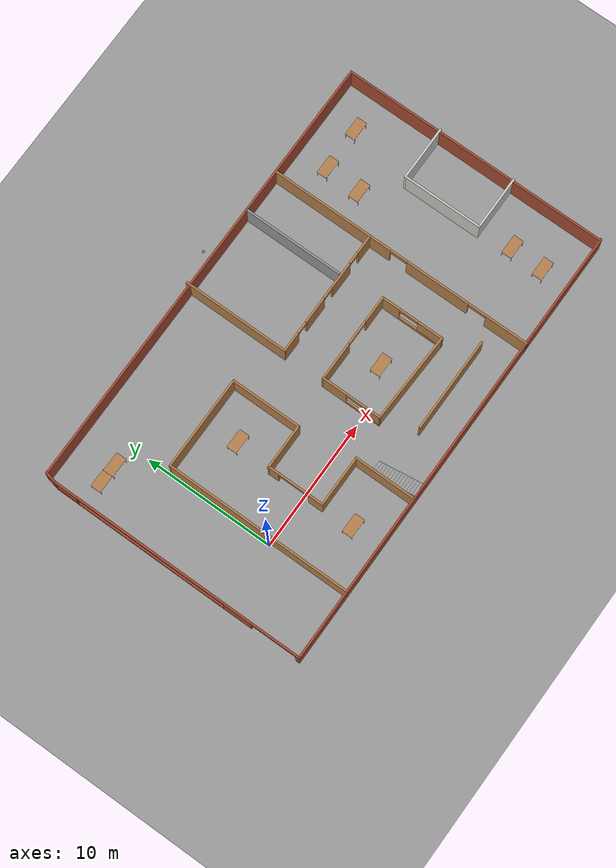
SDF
<sdf version="1.6">
 <world name="default">
  <light name="sun" type="directional">
   <pose>0 0 10 0 -0 0</pose>
   <diffuse>0.8 0.8 0.8 1</diffuse>
   <specular>0.2 0.2 0.2 1</specular>
   <attenuation>
    <range>1000</range>
    <constant>0.9</constant>
    <linear>0.01</linear>
    <quadratic>0.001</quadratic>
   </attenuation>
   <direction>-0.5 0.1 -0.9</direction>
  </light>
  <model name="ground_plane">
   <static>1</static>
   <link name="link">
    <collision name="collision">
     <geometry><plane><normal>0 0 1</normal><size>100 100</size></plane></geometry>
     <surface><friction><ode><mu>100</mu><mu2>50</mu2></ode></friction></surface>
    </collision>
    <visual name="visual">
     <cast_shadows>0</cast_shadows>
     <geometry><plane><normal>0 0 1</normal><size>100 100</size></plane></geometry>
     <material>
      <script><uri>file://media/materials/scripts/gazebo.material</uri><name>Gazebo/Grey</name></script>
     </material>
    </visual>
   </link>
  </model>
  <gravity>0 0 -9.8</gravity>
  <magnetic_field>6e-06 2.3e-05 -4.2e-05</magnetic_field>
  <atmosphere type="adiabatic"/>
  <physics name="default_physics" default="0" type="ode">
   <max_step_size>0.001</max_step_size>
   <real_time_factor>1</real_time_factor>
   <real_time_update_rate>1000</real_time_update_rate>
  </physics>
  <scene><ambient>0.4 0.4 0.4 1</ambient><background>0.7 0.7 0.7 1</background><shadows>1</shadows></scene>
  <spherical_coordinates>
   <surface_model>EARTH_WGS84</surface_model>
   <latitude_deg>0</latitude_deg>
   <longitude_deg>0</longitude_deg>
   <elevation>0</elevation>
   <heading_deg>0</heading_deg>
  </spherical_coordinates>
  <model name="mybuilding">
   <pose>12.3376 4.27138 0 0 -0 0</pose>
   <link name="Stairs_0">
    <visual name="Stairs_0_Visual_0">
     <pose>-3.86206 -7.02365 0.083333 0 -0 0</pose>
     <geometry><box><size>1 0.233333 0.166667</size></box></geometry>
     <material>
      <script><uri>file://media/materials/scripts/gazebo.material</uri><name>Gazebo/Grey</name></script>
      <ambient>1 1 1 1</ambient>
     </material>
     <meta><layer>0</layer></meta>
    </visual>
    <collision name="Stairs_0_Collision_0">
     <geometry><box><size>1 0.233333 0.166667</size></box></geometry>
     <pose>-3.86206 -7.02365 0.083333 0 -0 0</pose>
    </collision>
    <visual name="Stairs_0_Visual_1">
     <pose>-3.86206 -7.25699 0.25 0 -0 0</pose>
     <geometry><box><size>1 0.233333 0.166667</size></box></geometry>
     <material>
      <script><uri>file://media/materials/scripts/gazebo.material</uri><name>Gazebo/Grey</name></script>
      <ambient>1 1 1 1</ambient>
     </material>
     <meta><layer>0</layer></meta>
    </visual>
    <collision name="Stairs_0_Collision_1">
     <geometry><box><size>1 0.233333 0.166667</size></box></geometry>
     <pose>-3.86206 -7.25699 0.25 0 -0 0</pose>
    </collision>
    <visual name="Stairs_0_Visual_2">
     <pose>-3.86206 -7.49032 0.416667 0 -0 0</pose>
     <geometry><box><size>1 0.233333 0.166667</size></box></geometry>
     <material>
      <script><uri>file://media/materials/scripts/gazebo.material</uri><name>Gazebo/Grey</name></script>
      <ambient>1 1 1 1</ambient>
     </material>
     <meta><layer>0</layer></meta>
    </visual>
    <collision name="Stairs_0_Collision_2">
     <geometry><box><size>1 0.233333 0.166667</size></box></geometry>
     <pose>-3.86206 -7.49032 0.416667 0 -0 0</pose>
    </collision>
    <visual name="Stairs_0_Visual_3">
     <pose>-3.86206 -7.72365 0.583333 0 -0 0</pose>
     <geometry><box><size>1 0.233333 0.166667</size></box></geometry>
     <material>
      <script><uri>file://media/materials/scripts/gazebo.material</uri><name>Gazebo/Grey</name></script>
      <ambient>1 1 1 1</ambient>
     </material>
     <meta><layer>0</layer></meta>
    </visual>
    <collision name="Stairs_0_Collision_3">
     <geometry><box><size>1 0.233333 0.166667</size></box></geometry>
     <pose>-3.86206 -7.72365 0.583333 0 -0 0</pose>
    </collision>
    <visual name="Stairs_0_Visual_4">
     <pose>-3.86206 -7.95699 0.75 0 -0 0</pose>
     <geometry><box><size>1 0.233333 0.166667</size></box></geometry>
     <material>
      <script><uri>file://media/materials/scripts/gazebo.material</uri><name>Gazebo/Grey</name></script>
      <ambient>1 1 1 1</ambient>
     </material>
     <meta><layer>0</layer></meta>
    </visual>
    <collision name="Stairs_0_Collision_4">
     <geometry><box><size>1 0.233333 0.166667</size></box></geometry>
     <pose>-3.86206 -7.95699 0.75 0 -0 0</pose>
    </collision>
    <visual name="Stairs_0_Visual_5">
     <pose>-3.86206 -8.19032 0.916667 0 -0 0</pose>
     <geometry><box><size>1 0.233333 0.166667</size></box></geometry>
     <material>
      <script><uri>file://media/materials/scripts/gazebo.material</uri><name>Gazebo/Grey</name></script>
      <ambient>1 1 1 1</ambient>
     </material>
     <meta><layer>0</layer></meta>
    </visual>
    <collision name="Stairs_0_Collision_5">
     <geometry><box><size>1 0.233333 0.166667</size></box></geometry>
     <pose>-3.86206 -8.19032 0.916667 0 -0 0</pose>
    </collision>
    <visual name="Stairs_0_Visual_6">
     <pose>-3.86206 -8.42365 1.08333 0 -0 0</pose>
     <geometry><box><size>1 0.233333 0.166667</size></box></geometry>
     <material>
      <script><uri>file://media/materials/scripts/gazebo.material</uri><name>Gazebo/Grey</name></script>
      <ambient>1 1 1 1</ambient>
     </material>
     <meta><layer>0</layer></meta>
    </visual>
    <collision name="Stairs_0_Collision_6">
     <geometry><box><size>1 0.233333 0.166667</size></box></geometry>
     <pose>-3.86206 -8.42365 1.08333 0 -0 0</pose>
    </collision>
    <visual name="Stairs_0_Visual_7">
     <pose>-3.86206 -8.65699 1.25 0 -0 0</pose>
     <geometry><box><size>1 0.233333 0.166667</size></box></geometry>
     <material>
      <script><uri>file://media/materials/scripts/gazebo.material</uri><name>Gazebo/Grey</name></script>
      <ambient>1 1 1 1</ambient>
     </material>
     <meta><layer>0</layer></meta>
    </visual>
    <collision name="Stairs_0_Collision_7">
     <geometry><box><size>1 0.233333 0.166667</size></box></geometry>
     <pose>-3.86206 -8.65699 1.25 0 -0 0</pose>
    </collision>
    <visual name="Stairs_0_Visual_8">
     <pose>-3.86206 -8.89032 1.41667 0 -0 0</pose>
     <geometry><box><size>1 0.233333 0.166667</size></box></geometry>
     <material>
      <script><uri>file://media/materials/scripts/gazebo.material</uri><name>Gazebo/Grey</name></script>
      <ambient>1 1 1 1</ambient>
     </material>
     <meta><layer>0</layer></meta>
    </visual>
    <collision name="Stairs_0_Collision_8">
     <geometry><box><size>1 0.233333 0.166667</size></box></geometry>
     <pose>-3.86206 -8.89032 1.41667 0 -0 0</pose>
    </collision>
    <visual name="Stairs_0_Visual_9">
     <pose>-3.86206 -9.12365 1.58333 0 -0 0</pose>
     <geometry><box><size>1 0.233333 0.166667</size></box></geometry>
     <material>
      <script><uri>file://media/materials/scripts/gazebo.material</uri><name>Gazebo/Grey</name></script>
      <ambient>1 1 1 1</ambient>
     </material>
     <meta><layer>0</layer></meta>
    </visual>
    <collision name="Stairs_0_Collision_9">
     <geometry><box><size>1 0.233333 0.166667</size></box></geometry>
     <pose>-3.86206 -9.12365 1.58333 0 -0 0</pose>
    </collision>
    <visual name="Stairs_0_Visual_10">
     <pose>-3.86206 -9.35698 1.75 0 -0 0</pose>
     <geometry><box><size>1 0.233333 0.166667</size></box></geometry>
     <material>
      <script><uri>file://media/materials/scripts/gazebo.material</uri><name>Gazebo/Grey</name></script>
      <ambient>1 1 1 1</ambient>
     </material>
     <meta><layer>0</layer></meta>
    </visual>
    <collision name="Stairs_0_Collision_10">
     <geometry><box><size>1 0.233333 0.166667</size></box></geometry>
     <pose>-3.86206 -9.35698 1.75 0 -0 0</pose>
    </collision>
    <visual name="Stairs_0_Visual_11">
     <pose>-3.86206 -9.59032 1.91667 0 -0 0</pose>
     <geometry><box><size>1 0.233333 0.166667</size></box></geometry>
     <material>
      <script><uri>file://media/materials/scripts/gazebo.material</uri><name>Gazebo/Grey</name></script>
      <ambient>1 1 1 1</ambient>
     </material>
     <meta><layer>0</layer></meta>
    </visual>
    <collision name="Stairs_0_Collision_11">
     <geometry><box><size>1 0.233333 0.166667</size></box></geometry>
     <pose>-3.86206 -9.59032 1.91667 0 -0 0</pose>
    </collision>
    <visual name="Stairs_0_Visual_12">
     <pose>-3.86206 -9.82365 2.08333 0 -0 0</pose>
     <geometry><box><size>1 0.233333 0.166667</size></box></geometry>
     <material>
      <script><uri>file://media/materials/scripts/gazebo.material</uri><name>Gazebo/Grey</name></script>
      <ambient>1 1 1 1</ambient>
     </material>
     <meta><layer>0</layer></meta>
    </visual>
    <collision name="Stairs_0_Collision_12">
     <geometry><box><size>1 0.233333 0.166667</size></box></geometry>
     <pose>-3.86206 -9.82365 2.08333 0 -0 0</pose>
    </collision>
    <visual name="Stairs_0_Visual_13">
     <pose>-3.86206 -10.057 2.25 0 -0 0</pose>
     <geometry><box><size>1 0.233333 0.166667</size></box></geometry>
     <material>
      <script><uri>file://media/materials/scripts/gazebo.material</uri><name>Gazebo/Grey</name></script>
      <ambient>1 1 1 1</ambient>
     </material>
     <meta><layer>0</layer></meta>
    </visual>
    <collision name="Stairs_0_Collision_13">
     <geometry><box><size>1 0.233333 0.166667</size></box></geometry>
     <pose>-3.86206 -10.057 2.25 0 -0 0</pose>
    </collision>
    <visual name="Stairs_0_Visual_14">
     <pose>-3.86206 -10.2903 2.41667 0 -0 0</pose>
     <geometry><box><size>1 0.233333 0.166667</size></box></geometry>
     <material>
      <script><uri>file://media/materials/scripts/gazebo.material</uri><name>Gazebo/Grey</name></script>
      <ambient>1 1 1 1</ambient>
     </material>
     <meta><layer>0</layer></meta>
    </visual>
    <collision name="Stairs_0_Collision_14">
     <geometry><box><size>1 0.233333 0.166667</size></box></geometry>
     <pose>-3.86206 -10.2903 2.41667 0 -0 0</pose>
    </collision>
   </link>
   <link name="Wall_0">
    <pose>-17.4376 -0.526378 0 0 -0 1.5708</pose>
    <visual name="Wall_0_Visual_0">
     <pose>-9.83589 0 1.25 0 -0 0</pose>
     <geometry><box><size>0.328223 0.15 2.5</size></box></geometry>
     <material>
      <script><uri>file://media/materials/scripts/gazebo.material</uri><name>Gazebo/Bricks</name></script>
      <ambient>0.666667 1 1 1</ambient>
     </material>
     <meta><layer>0</layer></meta>
    </visual>
    <collision name="Wall_0_Collision_0">
     <geometry><box><size>0.328223 0.15 2.5</size></box></geometry>
     <pose>-9.83589 0 1.25 0 -0 0</pose>
    </collision>
    <visual name="Wall_0_Visual_1">
     <pose>-4.95614 0 1.25 0 -0 0</pose>
     <geometry><box><size>2.26813 0.15 2.5</size></box></geometry>
     <material>
      <script><uri>file://media/materials/scripts/gazebo.material</uri><name>Gazebo/Bricks</name></script>
      <ambient>0.666667 1 1 1</ambient>
     </material>
     <meta><layer>0</layer></meta>
    </visual>
    <collision name="Wall_0_Collision_1">
     <geometry><box><size>2.26813 0.15 2.5</size></box></geometry>
     <pose>-4.95614 0 1.25 0 -0 0</pose>
    </collision>
    <visual name="Wall_0_Visual_2">
     <pose>3.08896 0 0.25 0 -0 0</pose>
     <geometry><box><size>13.8221 0.15 0.5</size></box></geometry>
     <material>
      <script><uri>file://media/materials/scripts/gazebo.material</uri><name>Gazebo/Bricks</name></script>
      <ambient>0.666667 1 1 1</ambient>
     </material>
     <meta><layer>0</layer></meta>
    </visual>
    <collision name="Wall_0_Collision_2">
     <geometry><box><size>13.8221 0.15 0.5</size></box></geometry>
     <pose>3.08896 0 0.25 0 -0 0</pose>
    </collision>
    <visual name="Wall_0_Visual_3">
     <pose>9.08868 0 1.5 0 -0 0</pose>
     <geometry><box><size>1.82263 0.15 2</size></box></geometry>
     <material>
      <script><uri>file://media/materials/scripts/gazebo.material</uri><name>Gazebo/Bricks</name></script>
      <ambient>0.666667 1 1 1</ambient>
     </material>
     <meta><layer>0</layer></meta>
    </visual>
    <collision name="Wall_0_Collision_3">
     <geometry><box><size>1.82263 0.15 2</size></box></geometry>
     <pose>9.08868 0 1.5 0 -0 0</pose>
    </collision>
    <visual name="Wall_0_Visual_4">
     <pose>-7.88099 0 2.25 0 -0 0</pose>
     <geometry><box><size>3.58157 0.15 0.5</size></box></geometry>
     <material>
      <script><uri>file://media/materials/scripts/gazebo.material</uri><name>Gazebo/Bricks</name></script>
      <ambient>0.666667 1 1 1</ambient>
     </material>
     <meta><layer>0</layer></meta>
    </visual>
    <collision name="Wall_0_Collision_4">
     <geometry><box><size>3.58157 0.15 0.5</size></box></geometry>
     <pose>-7.88099 0 2.25 0 -0 0</pose>
    </collision>
    <visual name="Wall_0_Visual_5">
     <pose>2.17765 0 2.25 0 -0 0</pose>
     <geometry><box><size>11.9994 0.15 0.5</size></box></geometry>
     <material>
      <script><uri>file://media/materials/scripts/gazebo.material</uri><name>Gazebo/Bricks</name></script>
      <ambient>0.666667 1 1 1</ambient>
     </material>
     <meta><layer>0</layer></meta>
    </visual>
    <collision name="Wall_0_Collision_5">
     <geometry><box><size>11.9994 0.15 0.5</size></box></geometry>
     <pose>2.17765 0 2.25 0 -0 0</pose>
    </collision>
   </link>
   <link name="Wall_10">
    <collision name="Wall_10_Collision">
     <geometry><box><size>1.02253 0.15 2.5</size></box></geometry>
     <pose>0 0 1.25 0 -0 0</pose>
    </collision>
    <visual name="Wall_10_Visual">
     <pose>0 0 1.25 0 -0 0</pose>
     <geometry><box><size>1.02253 0.15 2.5</size></box></geometry>
     <material>
      <script><uri>file://media/materials/scripts/gazebo.material</uri><name>Gazebo/Bricks</name></script>
      <ambient>0.435294 0.796078 0.67451 1</ambient>
     </material>
     <meta><layer>0</layer></meta>
    </visual>
    <pose>-17.3541 9.82682 0 0 -0 1.3782</pose>
   </link>
   <link name="Wall_12">
    <collision name="Wall_12_Collision">
     <geometry><box><size>14.5 0.15 2.5</size></box></geometry>
     <pose>0 0 1.25 0 -0 0</pose>
    </collision>
    <visual name="Wall_12_Visual">
     <pose>0 0 1.25 0 -0 0</pose>
     <geometry><box><size>14.5 0.15 2.5</size></box></geometry>
     <material>
      <script><uri>file://media/materials/scripts/gazebo.material</uri><name>Gazebo/Wood</name></script>
      <ambient>1 1 1 1</ambient>
     </material>
     <meta><layer>0</layer></meta>
    </visual>
    <pose>-12.1051 -3.24089 0 0 -0 1.5708</pose>
   </link>
   <link name="Wall_13">
    <collision name="Wall_13_Collision">
     <geometry><box><size>7.25 0.15 2.5</size></box></geometry>
     <pose>0 0 1.25 0 -0 0</pose>
    </collision>
    <visual name="Wall_13_Visual">
     <pose>0 0 1.25 0 -0 0</pose>
     <geometry><box><size>7.25 0.15 2.5</size></box></geometry>
     <material>
      <script><uri>file://media/materials/scripts/gazebo.material</uri><name>Gazebo/Wood</name></script>
      <ambient>1 1 1 1</ambient>
     </material>
     <meta><layer>0</layer></meta>
    </visual>
    <pose>-8.55514 3.93411 0 0 -0 0</pose>
   </link>
   <link name="Wall_14">
    <collision name="Wall_14_Collision">
     <geometry><box><size>5.5 0.15 2.5</size></box></geometry>
     <pose>0 0 1.25 0 -0 0</pose>
    </collision>
    <visual name="Wall_14_Visual">
     <pose>0 0 1.25 0 -0 0</pose>
     <geometry><box><size>5.5 0.15 2.5</size></box></geometry>
     <material>
      <script><uri>file://media/materials/scripts/gazebo.material</uri><name>Gazebo/Wood</name></script>
      <ambient>1 1 1 1</ambient>
     </material>
     <meta><layer>0</layer></meta>
    </visual>
    <pose>-5.00514 1.25911 0 0 0 -1.5708</pose>
   </link>
   <link name="Wall_15">
    <collision name="Wall_15_Collision">
     <geometry><box><size>3.5 0.15 2.5</size></box></geometry>
     <pose>0 0 1.25 0 -0 0</pose>
    </collision>
    <visual name="Wall_15_Visual">
     <pose>0 0 1.25 0 -0 0</pose>
     <geometry><box><size>3.5 0.15 2.5</size></box></geometry>
     <material>
      <script><uri>file://media/materials/scripts/gazebo.material</uri><name>Gazebo/Wood</name></script>
      <ambient>1 1 1 1</ambient>
     </material>
     <meta><layer>0</layer></meta>
    </visual>
    <pose>-6.68015 -1.41589 0 0 -0 3.14159</pose>
   </link>
   <link name="Wall_16">
    <pose>-8.35515 -3.59089 0 0 0 -1.5708</pose>
    <visual name="Wall_16_Visual_0">
     <pose>-1.80371 0 1.25 0 -0 0</pose>
     <geometry><box><size>0.892589 0.15 2.5</size></box></geometry>
     <material>
      <script><uri>file://media/materials/scripts/gazebo.material</uri><name>Gazebo/Wood</name></script>
      <ambient>1 1 1 1</ambient>
     </material>
     <meta><layer>0</layer></meta>
    </visual>
    <collision name="Wall_16_Collision_0">
     <geometry><box><size>0.892589 0.15 2.5</size></box></geometry>
     <pose>-1.80371 0 1.25 0 -0 0</pose>
    </collision>
    <visual name="Wall_16_Visual_1">
     <pose>1.67277 0 1.25 0 -0 0</pose>
     <geometry><box><size>1.15445 0.15 2.5</size></box></geometry>
     <material>
      <script><uri>file://media/materials/scripts/gazebo.material</uri><name>Gazebo/Wood</name></script>
      <ambient>1 1 1 1</ambient>
     </material>
     <meta><layer>0</layer></meta>
    </visual>
    <collision name="Wall_16_Collision_1">
     <geometry><box><size>1.15445 0.15 2.5</size></box></geometry>
     <pose>1.67277 0 1.25 0 -0 0</pose>
    </collision>
    <visual name="Wall_16_Visual_2">
     <pose>-0.130931 0 2.25 0 -0 0</pose>
     <geometry><box><size>2.45296 0.15 0.5</size></box></geometry>
     <material>
      <script><uri>file://media/materials/scripts/gazebo.material</uri><name>Gazebo/Wood</name></script>
      <ambient>1 1 1 1</ambient>
     </material>
     <meta><layer>0</layer></meta>
    </visual>
    <collision name="Wall_16_Collision_2">
     <geometry><box><size>2.45296 0.15 0.5</size></box></geometry>
     <pose>-0.130931 0 2.25 0 -0 0</pose>
    </collision>
   </link>
   <link name="Wall_17">
    <collision name="Wall_17_Collision">
     <geometry><box><size>4 0.15 2.5</size></box></geometry>
     <pose>0 0 1.25 0 -0 0</pose>
    </collision>
    <visual name="Wall_17_Visual">
     <pose>0 0 1.25 0 -0 0</pose>
     <geometry><box><size>4 0.15 2.5</size></box></geometry>
     <material>
      <script><uri>file://media/materials/scripts/gazebo.material</uri><name>Gazebo/Wood</name></script>
      <ambient>1 1 1 1</ambient>
     </material>
     <meta><layer>0</layer></meta>
    </visual>
    <pose>-6.43015 -5.76589 0 0 -0 0</pose>
   </link>
   <link name="Wall_18">
    <collision name="Wall_18_Collision">
     <geometry><box><size>4.75 0.15 2.5</size></box></geometry>
     <pose>0 0 1.25 0 -0 0</pose>
    </collision>
    <visual name="Wall_18_Visual">
     <pose>0 0 1.25 0 -0 0</pose>
     <geometry><box><size>4.75 0.15 2.5</size></box></geometry>
     <material>
      <script><uri>file://media/materials/scripts/gazebo.material</uri><name>Gazebo/Wood</name></script>
      <ambient>1 1 1 1</ambient>
     </material>
     <meta><layer>0</layer></meta>
    </visual>
    <pose>-4.50514 -8.06589 0 0 0 -1.5708</pose>
   </link>
   <link name="Wall_2">
    <collision name="Wall_2_Collision">
     <geometry><box><size>35 0.15 2.5</size></box></geometry>
     <pose>0 0 1.25 0 -0 0</pose>
    </collision>
    <visual name="Wall_2_Visual">
     <pose>0 0 1.25 0 -0 0</pose>
     <geometry><box><size>35 0.15 2.5</size></box></geometry>
     <material>
      <script><uri>file://media/materials/scripts/gazebo.material</uri><name>Gazebo/Bricks</name></script>
      <ambient>0.666667 1 1 1</ambient>
     </material>
     <meta><layer>0</layer></meta>
    </visual>
    <pose>-0.012578 -10.4514 0 0 -0 0</pose>
   </link>
   <link name="Wall_20">
    <collision name="Wall_20_Collision">
     <geometry><box><size>8.25 0.15 2.5</size></box></geometry>
     <pose>0 0 1.25 0 -0 0</pose>
    </collision>
    <visual name="Wall_20_Visual">
     <pose>0 0 1.25 0 -0 0</pose>
     <geometry><box><size>8.25 0.15 2.5</size></box></geometry>
     <material>
      <script><uri>file://media/materials/scripts/gazebo.material</uri><name>Gazebo/Wood</name></script>
      <ambient>1 1 1 1</ambient>
     </material>
     <meta><layer>0</layer></meta>
    </visual>
    <pose>-1.34961 6.425 0 0 0 -1.5708</pose>
   </link>
   <link name="Wall_21">
    <pose>3.57539 2.375 0 0 -0 0</pose>
    <visual name="Wall_21_Visual_0">
     <pose>-4.20415 0 1.25 0 -0 0</pose>
     <geometry><box><size>1.5917 0.15 2.5</size></box></geometry>
     <material>
      <script><uri>file://media/materials/scripts/gazebo.material</uri><name>Gazebo/Wood</name></script>
      <ambient>1 1 1 1</ambient>
     </material>
     <meta><layer>0</layer></meta>
    </visual>
    <collision name="Wall_21_Collision_0">
     <geometry><box><size>1.5917 0.15 2.5</size></box></geometry>
     <pose>-4.20415 0 1.25 0 -0 0</pose>
    </collision>
    <visual name="Wall_21_Visual_1">
     <pose>-1.46063 0 1.25 0 -0 0</pose>
     <geometry><box><size>2.09534 0.15 2.5</size></box></geometry>
     <material>
      <script><uri>file://media/materials/scripts/gazebo.material</uri><name>Gazebo/Wood</name></script>
      <ambient>1 1 1 1</ambient>
     </material>
     <meta><layer>0</layer></meta>
    </visual>
    <collision name="Wall_21_Collision_1">
     <geometry><box><size>2.09534 0.15 2.5</size></box></geometry>
     <pose>-1.46063 0 1.25 0 -0 0</pose>
    </collision>
    <visual name="Wall_21_Visual_2">
     <pose>1.52422 0 1.25 0 -0 0</pose>
     <geometry><box><size>2.07438 0.15 2.5</size></box></geometry>
     <material>
      <script><uri>file://media/materials/scripts/gazebo.material</uri><name>Gazebo/Wood</name></script>
      <ambient>1 1 1 1</ambient>
     </material>
     <meta><layer>0</layer></meta>
    </visual>
    <collision name="Wall_21_Collision_2">
     <geometry><box><size>2.07438 0.15 2.5</size></box></geometry>
     <pose>1.52422 0 1.25 0 -0 0</pose>
    </collision>
    <visual name="Wall_21_Visual_3">
     <pose>4.23071 0 1.25 0 -0 0</pose>
     <geometry><box><size>1.53858 0.15 2.5</size></box></geometry>
     <material>
      <script><uri>file://media/materials/scripts/gazebo.material</uri><name>Gazebo/Wood</name></script>
      <ambient>1 1 1 1</ambient>
     </material>
     <meta><layer>0</layer></meta>
    </visual>
    <collision name="Wall_21_Collision_3">
     <geometry><box><size>1.53858 0.15 2.5</size></box></geometry>
     <pose>4.23071 0 1.25 0 -0 0</pose>
    </collision>
    <visual name="Wall_21_Visual_4">
     <pose>-2.9583 0 2.25 0 -0 0</pose>
     <geometry><box><size>0.9 0.15 0.5</size></box></geometry>
     <material>
      <script><uri>file://media/materials/scripts/gazebo.material</uri><name>Gazebo/Wood</name></script>
      <ambient>1 1 1 1</ambient>
     </material>
     <meta><layer>0</layer></meta>
    </visual>
    <collision name="Wall_21_Collision_4">
     <geometry><box><size>0.9 0.15 0.5</size></box></geometry>
     <pose>-2.9583 0 2.25 0 -0 0</pose>
    </collision>
    <visual name="Wall_21_Visual_5">
     <pose>0.037033 0 2.25 0 -0 0</pose>
     <geometry><box><size>0.9 0.15 0.5</size></box></geometry>
     <material>
      <script><uri>file://media/materials/scripts/gazebo.material</uri><name>Gazebo/Wood</name></script>
      <ambient>1 1 1 1</ambient>
     </material>
     <meta><layer>0</layer></meta>
    </visual>
    <collision name="Wall_21_Collision_5">
     <geometry><box><size>0.9 0.15 0.5</size></box></geometry>
     <pose>0.037033 0 2.25 0 -0 0</pose>
    </collision>
    <visual name="Wall_21_Visual_6">
     <pose>3.01142 0 2.25 0 -0 0</pose>
     <geometry><box><size>0.9 0.15 0.5</size></box></geometry>
     <material>
      <script><uri>file://media/materials/scripts/gazebo.material</uri><name>Gazebo/Wood</name></script>
      <ambient>1 1 1 1</ambient>
     </material>
     <meta><layer>0</layer></meta>
    </visual>
    <collision name="Wall_21_Collision_6">
     <geometry><box><size>0.9 0.15 0.5</size></box></geometry>
     <pose>3.01142 0 2.25 0 -0 0</pose>
    </collision>
   </link>
   <link name="Wall_25">
    <collision name="Wall_25_Collision">
     <geometry><box><size>8 0.15 2.5</size></box></geometry>
     <pose>0 0 1.25 0 -0 0</pose>
    </collision>
    <visual name="Wall_25_Visual">
     <pose>0 0 1.25 0 -0 0</pose>
     <geometry><box><size>8 0.15 2.5</size></box></geometry>
     <material>
      <script><uri>file://media/materials/scripts/gazebo.material</uri><name>Gazebo/Wood</name></script>
      <ambient>1 1 1 1</ambient>
     </material>
     <meta><layer>0</layer></meta>
    </visual>
    <pose>8.50039 6.3 0 0 -0 1.5708</pose>
   </link>
   <link name="Wall_29">
    <pose>8.50039 -4.05 0 0 0 -1.5708</pose>
    <visual name="Wall_29_Visual_0">
     <pose>-5.605 0 1.25 0 -0 0</pose>
     <geometry><box><size>1.79001 0.15 2.5</size></box></geometry>
     <material>
      <script><uri>file://media/materials/scripts/gazebo.material</uri><name>Gazebo/Wood</name></script>
      <ambient>1 1 1 1</ambient>
     </material>
     <meta><layer>0</layer></meta>
    </visual>
    <collision name="Wall_29_Collision_0">
     <geometry><box><size>1.79001 0.15 2.5</size></box></geometry>
     <pose>-5.605 0 1.25 0 -0 0</pose>
    </collision>
    <visual name="Wall_29_Visual_1">
     <pose>-0.813872 0 1.25 0 -0 0</pose>
     <geometry><box><size>5.05087 0.15 2.5</size></box></geometry>
     <material>
      <script><uri>file://media/materials/scripts/gazebo.material</uri><name>Gazebo/Wood</name></script>
      <ambient>1 1 1 1</ambient>
     </material>
     <meta><layer>0</layer></meta>
    </visual>
    <collision name="Wall_29_Collision_1">
     <geometry><box><size>5.05087 0.15 2.5</size></box></geometry>
     <pose>-0.813872 0 1.25 0 -0 0</pose>
    </collision>
    <visual name="Wall_29_Visual_2">
     <pose>4.82475 0 1.25 0 -0 0</pose>
     <geometry><box><size>3.35051 0.15 2.5</size></box></geometry>
     <material>
      <script><uri>file://media/materials/scripts/gazebo.material</uri><name>Gazebo/Wood</name></script>
      <ambient>1 1 1 1</ambient>
     </material>
     <meta><layer>0</layer></meta>
    </visual>
    <collision name="Wall_29_Collision_2">
     <geometry><box><size>3.35051 0.15 2.5</size></box></geometry>
     <pose>4.82475 0 1.25 0 -0 0</pose>
    </collision>
    <visual name="Wall_29_Visual_3">
     <pose>-4.02465 0 2.25 0 -0 0</pose>
     <geometry><box><size>1.37069 0.15 0.5</size></box></geometry>
     <material>
      <script><uri>file://media/materials/scripts/gazebo.material</uri><name>Gazebo/Wood</name></script>
      <ambient>1 1 1 1</ambient>
     </material>
     <meta><layer>0</layer></meta>
    </visual>
    <collision name="Wall_29_Collision_3">
     <geometry><box><size>1.37069 0.15 0.5</size></box></geometry>
     <pose>-4.02465 0 2.25 0 -0 0</pose>
    </collision>
    <visual name="Wall_29_Visual_4">
     <pose>2.43053 0 2.25 0 -0 0</pose>
     <geometry><box><size>1.43793 0.15 0.5</size></box></geometry>
     <material>
      <script><uri>file://media/materials/scripts/gazebo.material</uri><name>Gazebo/Wood</name></script>
      <ambient>1 1 1 1</ambient>
     </material>
     <meta><layer>0</layer></meta>
    </visual>
    <collision name="Wall_29_Collision_4">
     <geometry><box><size>1.43793 0.15 0.5</size></box></geometry>
     <pose>2.43053 0 2.25 0 -0 0</pose>
    </collision>
   </link>
   <link name="Wall_31">
    <collision name="Wall_31_Collision">
     <geometry><box><size>4.25 0.15 2.5</size></box></geometry>
     <pose>0 0 1.25 0 -0 0</pose>
    </collision>
    <visual name="Wall_31_Visual">
     <pose>0 0 1.25 0 -0 0</pose>
     <geometry><box><size>4.25 0.15 2.5</size></box></geometry>
     <material>
      <script><uri>file://media/materials/scripts/gazebo.material</uri><name>Gazebo/CeilingTiled</name></script>
      <ambient>0.435294 0.796078 0.67451 1</ambient>
     </material>
     <meta><layer>0</layer></meta>
    </visual>
    <pose>15.4005 2.85446 0 0 -0 3.14159</pose>
   </link>
   <link name="Wall_32">
    <collision name="Wall_32_Collision">
     <geometry><box><size>6.25 0.15 2.5</size></box></geometry>
     <pose>0 0 1.25 0 -0 0</pose>
    </collision>
    <visual name="Wall_32_Visual">
     <pose>0 0 1.25 0 -0 0</pose>
     <geometry><box><size>6.25 0.15 2.5</size></box></geometry>
     <material>
      <script><uri>file://media/materials/scripts/gazebo.material</uri><name>Gazebo/CeilingTiled</name></script>
      <ambient>0.435294 0.796078 0.67451 1</ambient>
     </material>
     <meta><layer>0</layer></meta>
    </visual>
    <pose>13.3505 -0.195546 0 0 0 -1.5708</pose>
   </link>
   <link name="Wall_33">
    <collision name="Wall_33_Collision">
     <geometry><box><size>4.25 0.15 2.5</size></box></geometry>
     <pose>0 0 1.25 0 -0 0</pose>
    </collision>
    <visual name="Wall_33_Visual">
     <pose>0 0 1.25 0 -0 0</pose>
     <geometry><box><size>4.25 0.15 2.5</size></box></geometry>
     <material>
      <script><uri>file://media/materials/scripts/gazebo.material</uri><name>Gazebo/CeilingTiled</name></script>
      <ambient>0.435294 0.796078 0.67451 1</ambient>
     </material>
     <meta><layer>0</layer></meta>
    </visual>
    <pose>15.4005 -3.24555 0 0 -0 0</pose>
   </link>
   <link name="Wall_35">
    <collision name="Wall_35_Collision">
     <geometry><box><size>7.25 0.15 2.5</size></box></geometry>
     <pose>0 0 1.25 0 -0 0</pose>
    </collision>
    <visual name="Wall_35_Visual">
     <pose>0 0 1.25 0 -0 0</pose>
     <geometry><box><size>7.25 0.15 2.5</size></box></geometry>
     <material>
      <script><uri>file://media/materials/scripts/gazebo.material</uri><name>Gazebo/Wood</name></script>
      <ambient>1 1 1 1</ambient>
     </material>
     <meta><layer>0</layer></meta>
    </visual>
    <pose>3.24004 -7.99919 0 0 -0 0</pose>
   </link>
   <link name="Wall_37">
    <pose>2.06257 -0.829206 0 0 -0 0</pose>
    <visual name="Wall_37_Visual_0">
     <pose>-2.00216 0 1.25 0 -0 0</pose>
     <geometry><box><size>2.99569 0.15 2.5</size></box></geometry>
     <material>
      <script><uri>file://media/materials/scripts/gazebo.material</uri><name>Gazebo/Wood</name></script>
      <ambient>1 1 1 1</ambient>
     </material>
     <meta><layer>0</layer></meta>
    </visual>
    <collision name="Wall_37_Collision_0">
     <geometry><box><size>2.99569 0.15 2.5</size></box></geometry>
     <pose>-2.00216 0 1.25 0 -0 0</pose>
    </collision>
    <visual name="Wall_37_Visual_1">
     <pose>2.45215 0 1.25 0 -0 0</pose>
     <geometry><box><size>2.09569 0.15 2.5</size></box></geometry>
     <material>
      <script><uri>file://media/materials/scripts/gazebo.material</uri><name>Gazebo/Wood</name></script>
      <ambient>1 1 1 1</ambient>
     </material>
     <meta><layer>0</layer></meta>
    </visual>
    <collision name="Wall_37_Collision_1">
     <geometry><box><size>2.09569 0.15 2.5</size></box></geometry>
     <pose>2.45215 0 1.25 0 -0 0</pose>
    </collision>
    <visual name="Wall_37_Visual_2">
     <pose>0.45 0 2.25 0 -0 0</pose>
     <geometry><box><size>1.90862 0.15 0.5</size></box></geometry>
     <material>
      <script><uri>file://media/materials/scripts/gazebo.material</uri><name>Gazebo/Wood</name></script>
      <ambient>1 1 1 1</ambient>
     </material>
     <meta><layer>0</layer></meta>
    </visual>
    <collision name="Wall_37_Collision_2">
     <geometry><box><size>1.90862 0.15 0.5</size></box></geometry>
     <pose>0.45 0 2.25 0 -0 0</pose>
    </collision>
   </link>
   <link name="Wall_38">
    <pose>5.48757 -3.25421 0 0 0 -1.5708</pose>
    <visual name="Wall_38_Visual_0">
     <pose>-1.75171 0 1.25 0 -0 0</pose>
     <geometry><box><size>1.49658 0.15 2.5</size></box></geometry>
     <material>
      <script><uri>file://media/materials/scripts/gazebo.material</uri><name>Gazebo/Wood</name></script>
      <ambient>1 1 1 1</ambient>
     </material>
     <meta><layer>0</layer></meta>
    </visual>
    <collision name="Wall_38_Collision_0">
     <geometry><box><size>1.49658 0.15 2.5</size></box></geometry>
     <pose>-1.75171 0 1.25 0 -0 0</pose>
    </collision>
    <visual name="Wall_38_Visual_1">
     <pose>0.748289 0 0.25 0 -0 0</pose>
     <geometry><box><size>3.50342 0.15 0.5</size></box></geometry>
     <material>
      <script><uri>file://media/materials/scripts/gazebo.material</uri><name>Gazebo/Wood</name></script>
      <ambient>1 1 1 1</ambient>
     </material>
     <meta><layer>0</layer></meta>
    </visual>
    <collision name="Wall_38_Collision_1">
     <geometry><box><size>3.50342 0.15 0.5</size></box></geometry>
     <pose>0.748289 0 0.25 0 -0 0</pose>
    </collision>
    <visual name="Wall_38_Visual_2">
     <pose>1.49829 0 1.5 0 -0 0</pose>
     <geometry><box><size>2.00342 0.15 2</size></box></geometry>
     <material>
      <script><uri>file://media/materials/scripts/gazebo.material</uri><name>Gazebo/Wood</name></script>
      <ambient>1 1 1 1</ambient>
     </material>
     <meta><layer>0</layer></meta>
    </visual>
    <collision name="Wall_38_Collision_2">
     <geometry><box><size>2.00342 0.15 2</size></box></geometry>
     <pose>1.49829 0 1.5 0 -0 0</pose>
    </collision>
    <visual name="Wall_38_Visual_3">
     <pose>-0.253423 0 2.25 0 -0 0</pose>
     <geometry><box><size>1.5 0.15 0.5</size></box></geometry>
     <material>
      <script><uri>file://media/materials/scripts/gazebo.material</uri><name>Gazebo/Wood</name></script>
      <ambient>1 1 1 1</ambient>
     </material>
     <meta><layer>0</layer></meta>
    </visual>
    <collision name="Wall_38_Collision_3">
     <geometry><box><size>1.5 0.15 0.5</size></box></geometry>
     <pose>-0.253423 0 2.25 0 -0 0</pose>
    </collision>
   </link>
   <link name="Wall_4">
    <collision name="Wall_4_Collision">
     <geometry><box><size>20.75 0.15 2.5</size></box></geometry>
     <pose>0 0 1.25 0 -0 0</pose>
    </collision>
    <visual name="Wall_4_Visual">
     <pose>0 0 1.25 0 -0 0</pose>
     <geometry><box><size>20.75 0.15 2.5</size></box></geometry>
     <material>
      <script><uri>file://media/materials/scripts/gazebo.material</uri><name>Gazebo/Bricks</name></script>
      <ambient>1 1 1 1</ambient>
     </material>
     <meta><layer>0</layer></meta>
    </visual>
    <pose>17.3294 -0.044979 0 0 -0 1.5708</pose>
   </link>
   <link name="Wall_42">
    <pose>-1.36244 -3.12921 0 0 0 -1.5708</pose>
    <visual name="Wall_42_Visual_0">
     <pose>-1.37456 0 1.25 0 -0 0</pose>
     <geometry><box><size>2.00089 0.15 2.5</size></box></geometry>
     <material>
      <script><uri>file://media/materials/scripts/gazebo.material</uri><name>Gazebo/Wood</name></script>
      <ambient>1 1 1 1</ambient>
     </material>
     <meta><layer>0</layer></meta>
    </visual>
    <collision name="Wall_42_Collision_0">
     <geometry><box><size>2.00089 0.15 2.5</size></box></geometry>
     <pose>-1.37456 0 1.25 0 -0 0</pose>
    </collision>
    <visual name="Wall_42_Visual_1">
     <pose>1.00044 0 0.25 0 -0 0</pose>
     <geometry><box><size>2.74911 0.15 0.5</size></box></geometry>
     <material>
      <script><uri>file://media/materials/scripts/gazebo.material</uri><name>Gazebo/Wood</name></script>
      <ambient>1 1 1 1</ambient>
     </material>
     <meta><layer>0</layer></meta>
    </visual>
    <collision name="Wall_42_Collision_1">
     <geometry><box><size>2.74911 0.15 0.5</size></box></geometry>
     <pose>1.00044 0 0.25 0 -0 0</pose>
    </collision>
    <visual name="Wall_42_Visual_2">
     <pose>1.75044 0 1.5 0 -0 0</pose>
     <geometry><box><size>1.24911 0.15 2</size></box></geometry>
     <material>
      <script><uri>file://media/materials/scripts/gazebo.material</uri><name>Gazebo/Wood</name></script>
      <ambient>1 1 1 1</ambient>
     </material>
     <meta><layer>0</layer></meta>
    </visual>
    <collision name="Wall_42_Collision_2">
     <geometry><box><size>1.24911 0.15 2</size></box></geometry>
     <pose>1.75044 0 1.5 0 -0 0</pose>
    </collision>
    <visual name="Wall_42_Visual_3">
     <pose>0.375888 0 2.25 0 -0 0</pose>
     <geometry><box><size>1.5 0.15 0.5</size></box></geometry>
     <material>
      <script><uri>file://media/materials/scripts/gazebo.material</uri><name>Gazebo/Wood</name></script>
      <ambient>1 1 1 1</ambient>
     </material>
     <meta><layer>0</layer></meta>
    </visual>
    <collision name="Wall_42_Collision_3">
     <geometry><box><size>1.5 0.15 0.5</size></box></geometry>
     <pose>0.375888 0 2.25 0 -0 0</pose>
    </collision>
   </link>
   <link name="Wall_43">
    <collision name="Wall_43_Collision">
     <geometry><box><size>7.00456 0.15 2.5</size></box></geometry>
     <pose>0 0 1.25 0 -0 0</pose>
    </collision>
    <visual name="Wall_43_Visual">
     <pose>0 0 1.25 0 -0 0</pose>
     <geometry><box><size>7.00456 0.15 2.5</size></box></geometry>
     <material>
      <script><uri>file://media/materials/scripts/gazebo.material</uri><name>Gazebo/Wood</name></script>
      <ambient>1 1 1 1</ambient>
     </material>
     <meta><layer>0</layer></meta>
    </visual>
    <pose>2.06257 -5.55421 0 0 0 -0.03648</pose>
   </link>
   <link name="Wall_46">
    <collision name="Wall_46_Collision">
     <geometry><box><size>7.75 0.15 2.5</size></box></geometry>
     <pose>0 0 1.25 0 -0 0</pose>
    </collision>
    <visual name="Wall_46_Visual">
     <pose>0 0 1.25 0 -0 0</pose>
     <geometry><box><size>7.75 0.15 2.5</size></box></geometry>
     <material>
      <script><uri>file://media/materials/scripts/gazebo.material</uri><name>Gazebo/Grey</name></script>
      <ambient>1 1 1 1</ambient>
     </material>
     <meta><layer>0</layer></meta>
    </visual>
    <pose>5.14189 6.38682 0 0 -0 1.5708</pose>
   </link>
   <link name="Wall_8">
    <collision name="Wall_8_Collision">
     <geometry><box><size>34.75 0.15 2.5</size></box></geometry>
     <pose>0 0 1.25 0 -0 0</pose>
    </collision>
    <visual name="Wall_8_Visual">
     <pose>0 0 1.25 0 -0 0</pose>
     <geometry><box><size>34.75 0.15 2.5</size></box></geometry>
     <material>
      <script><uri>file://media/materials/scripts/gazebo.material</uri><name>Gazebo/Bricks</name></script>
      <ambient>0.666667 1 1 1</ambient>
     </material>
     <meta><layer>0</layer></meta>
    </visual>
    <pose>0.029431 10.255 0 0 -0 3.14159</pose>
   </link>
   <static>1</static>
  </model>
  <model name="ground_plane_0">
   <static>1</static>
   <link name="link">
    <collision name="collision">
     <geometry><plane><normal>0 0 1</normal><size>100 100</size></plane></geometry>
     <surface><friction><ode><mu>100</mu><mu2>50</mu2></ode></friction></surface>
    </collision>
    <visual name="visual">
     <cast_shadows>0</cast_shadows>
     <geometry><plane><normal>0 0 1</normal><size>100 100</size></plane></geometry>
     <material>
      <script><uri>file://media/materials/scripts/gazebo.material</uri><name>Gazebo/Grey</name></script>
     </material>
    </visual>
   </link>
   <pose>14.9212 -1.71168 0 0 -0 0</pose>
  </model>
  <model name="table">
   <static>1</static>
   <link name="link">
    <collision name="surface">
     <pose>0 0 1 0 -0 0</pose>
     <geometry><box><size>1.5 0.8 0.03</size></box></geometry>
     <surface><friction><ode><mu>0.6</mu><mu2>0.6</mu2></ode></friction></surface>
    </collision>
    <visual name="visual1">
     <pose>0 0 1 0 -0 0</pose>
     <geometry><box><size>1.5 0.8 0.03</size></box></geometry>
     <material>
      <script><uri>file://media/materials/scripts/gazebo.material</uri><name>Gazebo/Wood</name></script>
     </material>
    </visual>
    <collision name="front_left_leg">
     <pose>0.68 0.38 0.5 0 -0 0</pose>
     <geometry><cylinder><radius>0.02</radius><length>1</length></cylinder></geometry>
    </collision>
    <visual name="front_left_leg">
     <pose>0.68 0.38 0.5 0 -0 0</pose>
     <geometry><cylinder><radius>0.02</radius><length>1</length></cylinder></geometry>
     <material>
      <script><uri>file://media/materials/scripts/gazebo.material</uri><name>Gazebo/Grey</name></script>
     </material>
    </visual>
    <collision name="front_right_leg">
     <pose>0.68 -0.38 0.5 0 -0 0</pose>
     <geometry><cylinder><radius>0.02</radius><length>1</length></cylinder></geometry>
    </collision>
    <visual name="front_right_leg">
     <pose>0.68 -0.38 0.5 0 -0 0</pose>
     <geometry><cylinder><radius>0.02</radius><length>1</length></cylinder></geometry>
     <material>
      <script><uri>file://media/materials/scripts/gazebo.material</uri><name>Gazebo/Grey</name></script>
     </material>
    </visual>
    <collision name="back_right_leg">
     <pose>-0.68 -0.38 0.5 0 -0 0</pose>
     <geometry><cylinder><radius>0.02</radius><length>1</length></cylinder></geometry>
    </collision>
    <visual name="back_right_leg">
     <pose>-0.68 -0.38 0.5 0 -0 0</pose>
     <geometry><cylinder><radius>0.02</radius><length>1</length></cylinder></geometry>
     <material>
      <script><uri>file://media/materials/scripts/gazebo.material</uri><name>Gazebo/Grey</name></script>
     </material>
    </visual>
    <collision name="back_left_leg">
     <pose>-0.68 0.38 0.5 0 -0 0</pose>
     <geometry><cylinder><radius>0.02</radius><length>1</length></cylinder></geometry>
    </collision>
    <visual name="back_left_leg">
     <pose>-0.68 0.38 0.5 0 -0 0</pose>
     <geometry><cylinder><radius>0.02</radius><length>1</length></cylinder></geometry>
     <material>
      <script><uri>file://media/materials/scripts/gazebo.material</uri><name>Gazebo/Grey</name></script>
     </material>
    </visual>
   </link>
   <pose>4.38032 5.74371 0 0 -0 0</pose>
  </model>
  <model name="table_clone">
   <static>1</static>
   <link name="link">
    <collision name="surface">
     <pose>0 0 1 0 -0 0</pose>
     <geometry><box><size>1.5 0.8 0.03</size></box></geometry>
     <surface><friction><ode><mu>0.6</mu><mu2>0.6</mu2></ode></friction></surface>
    </collision>
    <visual name="visual1">
     <pose>0 0 1 0 -0 0</pose>
     <geometry><box><size>1.5 0.8 0.03</size></box></geometry>
     <material>
      <script><uri>file://media/materials/scripts/gazebo.material</uri><name>Gazebo/Wood</name></script>
     </material>
    </visual>
    <collision name="front_left_leg">
     <pose>0.68 0.38 0.5 0 -0 0</pose>
     <geometry><cylinder><radius>0.02</radius><length>1</length></cylinder></geometry>
    </collision>
    <visual name="front_left_leg">
     <pose>0.68 0.38 0.5 0 -0 0</pose>
     <geometry><cylinder><radius>0.02</radius><length>1</length></cylinder></geometry>
     <material>
      <script><uri>file://media/materials/scripts/gazebo.material</uri><name>Gazebo/Grey</name></script>
     </material>
    </visual>
    <collision name="front_right_leg">
     <pose>0.68 -0.38 0.5 0 -0 0</pose>
     <geometry><cylinder><radius>0.02</radius><length>1</length></cylinder></geometry>
    </collision>
    <visual name="front_right_leg">
     <pose>0.68 -0.38 0.5 0 -0 0</pose>
     <geometry><cylinder><radius>0.02</radius><length>1</length></cylinder></geometry>
     <material>
      <script><uri>file://media/materials/scripts/gazebo.material</uri><name>Gazebo/Grey</name></script>
     </material>
    </visual>
    <collision name="back_right_leg">
     <pose>-0.68 -0.38 0.5 0 -0 0</pose>
     <geometry><cylinder><radius>0.02</radius><length>1</length></cylinder></geometry>
    </collision>
    <visual name="back_right_leg">
     <pose>-0.68 -0.38 0.5 0 -0 0</pose>
     <geometry><cylinder><radius>0.02</radius><length>1</length></cylinder></geometry>
     <material>
      <script><uri>file://media/materials/scripts/gazebo.material</uri><name>Gazebo/Grey</name></script>
     </material>
    </visual>
    <collision name="back_left_leg">
     <pose>-0.68 0.38 0.5 0 -0 0</pose>
     <geometry><cylinder><radius>0.02</radius><length>1</length></cylinder></geometry>
    </collision>
    <visual name="back_left_leg">
     <pose>-0.68 0.38 0.5 0 -0 0</pose>
     <geometry><cylinder><radius>0.02</radius><length>1</length></cylinder></geometry>
     <material>
      <script><uri>file://media/materials/scripts/gazebo.material</uri><name>Gazebo/Grey</name></script>
     </material>
    </visual>
   </link>
   <pose>4.23361 -3.85679 0 0 -0 0</pose>
  </model>
  <model name="table_clone_0">
   <static>1</static>
   <link name="link">
    <collision name="surface">
     <pose>0 0 1 0 -0 0</pose>
     <geometry><box><size>1.5 0.8 0.03</size></box></geometry>
     <surface><friction><ode><mu>0.6</mu><mu2>0.6</mu2></ode></friction></surface>
    </collision>
    <visual name="visual1">
     <pose>0 0 1 0 -0 0</pose>
     <geometry><box><size>1.5 0.8 0.03</size></box></geometry>
     <material>
      <script><uri>file://media/materials/scripts/gazebo.material</uri><name>Gazebo/Wood</name></script>
     </material>
    </visual>
    <collision name="front_left_leg">
     <pose>0.68 0.38 0.5 0 -0 0</pose>
     <geometry><cylinder><radius>0.02</radius><length>1</length></cylinder></geometry>
    </collision>
    <visual name="front_left_leg">
     <pose>0.68 0.38 0.5 0 -0 0</pose>
     <geometry><cylinder><radius>0.02</radius><length>1</length></cylinder></geometry>
     <material>
      <script><uri>file://media/materials/scripts/gazebo.material</uri><name>Gazebo/Grey</name></script>
     </material>
    </visual>
    <collision name="front_right_leg">
     <pose>0.68 -0.38 0.5 0 -0 0</pose>
     <geometry><cylinder><radius>0.02</radius><length>1</length></cylinder></geometry>
    </collision>
    <visual name="front_right_leg">
     <pose>0.68 -0.38 0.5 0 -0 0</pose>
     <geometry><cylinder><radius>0.02</radius><length>1</length></cylinder></geometry>
     <material>
      <script><uri>file://media/materials/scripts/gazebo.material</uri><name>Gazebo/Grey</name></script>
     </material>
    </visual>
    <collision name="back_right_leg">
     <pose>-0.68 -0.38 0.5 0 -0 0</pose>
     <geometry><cylinder><radius>0.02</radius><length>1</length></cylinder></geometry>
    </collision>
    <visual name="back_right_leg">
     <pose>-0.68 -0.38 0.5 0 -0 0</pose>
     <geometry><cylinder><radius>0.02</radius><length>1</length></cylinder></geometry>
     <material>
      <script><uri>file://media/materials/scripts/gazebo.material</uri><name>Gazebo/Grey</name></script>
     </material>
    </visual>
    <collision name="back_left_leg">
     <pose>-0.68 0.38 0.5 0 -0 0</pose>
     <geometry><cylinder><radius>0.02</radius><length>1</length></cylinder></geometry>
    </collision>
    <visual name="back_left_leg">
     <pose>-0.68 0.38 0.5 0 -0 0</pose>
     <geometry><cylinder><radius>0.02</radius><length>1</length></cylinder></geometry>
     <material>
      <script><uri>file://media/materials/scripts/gazebo.material</uri><name>Gazebo/Grey</name></script>
     </material>
    </visual>
   </link>
   <pose>26.2534 -1.46858 0 0 -0 0</pose>
  </model>
  <model name="table_clone_0_clone">
   <static>1</static>
   <link name="link">
    <collision name="surface">
     <pose>0 0 1 0 -0 0</pose>
     <geometry><box><size>1.5 0.8 0.03</size></box></geometry>
     <surface><friction><ode><mu>0.6</mu><mu2>0.6</mu2></ode></friction></surface>
    </collision>
    <visual name="visual1">
     <pose>0 0 1 0 -0 0</pose>
     <geometry><box><size>1.5 0.8 0.03</size></box></geometry>
     <material>
      <script><uri>file://media/materials/scripts/gazebo.material</uri><name>Gazebo/Wood</name></script>
     </material>
    </visual>
    <collision name="front_left_leg">
     <pose>0.68 0.38 0.5 0 -0 0</pose>
     <geometry><cylinder><radius>0.02</radius><length>1</length></cylinder></geometry>
    </collision>
    <visual name="front_left_leg">
     <pose>0.68 0.38 0.5 0 -0 0</pose>
     <geometry><cylinder><radius>0.02</radius><length>1</length></cylinder></geometry>
     <material>
      <script><uri>file://media/materials/scripts/gazebo.material</uri><name>Gazebo/Grey</name></script>
     </material>
    </visual>
    <collision name="front_right_leg">
     <pose>0.68 -0.38 0.5 0 -0 0</pose>
     <geometry><cylinder><radius>0.02</radius><length>1</length></cylinder></geometry>
    </collision>
    <visual name="front_right_leg">
     <pose>0.68 -0.38 0.5 0 -0 0</pose>
     <geometry><cylinder><radius>0.02</radius><length>1</length></cylinder></geometry>
     <material>
      <script><uri>file://media/materials/scripts/gazebo.material</uri><name>Gazebo/Grey</name></script>
     </material>
    </visual>
    <collision name="back_right_leg">
     <pose>-0.68 -0.38 0.5 0 -0 0</pose>
     <geometry><cylinder><radius>0.02</radius><length>1</length></cylinder></geometry>
    </collision>
    <visual name="back_right_leg">
     <pose>-0.68 -0.38 0.5 0 -0 0</pose>
     <geometry><cylinder><radius>0.02</radius><length>1</length></cylinder></geometry>
     <material>
      <script><uri>file://media/materials/scripts/gazebo.material</uri><name>Gazebo/Grey</name></script>
     </material>
    </visual>
    <collision name="back_left_leg">
     <pose>-0.68 0.38 0.5 0 -0 0</pose>
     <geometry><cylinder><radius>0.02</radius><length>1</length></cylinder></geometry>
    </collision>
    <visual name="back_left_leg">
     <pose>-0.68 0.38 0.5 0 -0 0</pose>
     <geometry><cylinder><radius>0.02</radius><length>1</length></cylinder></geometry>
     <material>
      <script><uri>file://media/materials/scripts/gazebo.material</uri><name>Gazebo/Grey</name></script>
     </material>
    </visual>
   </link>
   <pose>26.1826 -4.01135 0 0 -0 0</pose>
  </model>
  <model name="table_clone_0_clone_0">
   <static>1</static>
   <link name="link">
    <collision name="surface">
     <pose>0 0 1 0 -0 0</pose>
     <geometry><box><size>1.5 0.8 0.03</size></box></geometry>
     <surface><friction><ode><mu>0.6</mu><mu2>0.6</mu2></ode></friction></surface>
    </collision>
    <visual name="visual1">
     <pose>0 0 1 0 -0 0</pose>
     <geometry><box><size>1.5 0.8 0.03</size></box></geometry>
     <material>
      <script><uri>file://media/materials/scripts/gazebo.material</uri><name>Gazebo/Wood</name></script>
     </material>
    </visual>
    <collision name="front_left_leg">
     <pose>0.68 0.38 0.5 0 -0 0</pose>
     <geometry><cylinder><radius>0.02</radius><length>1</length></cylinder></geometry>
    </collision>
    <visual name="front_left_leg">
     <pose>0.68 0.38 0.5 0 -0 0</pose>
     <geometry><cylinder><radius>0.02</radius><length>1</length></cylinder></geometry>
     <material>
      <script><uri>file://media/materials/scripts/gazebo.material</uri><name>Gazebo/Grey</name></script>
     </material>
    </visual>
    <collision name="front_right_leg">
     <pose>0.68 -0.38 0.5 0 -0 0</pose>
     <geometry><cylinder><radius>0.02</radius><length>1</length></cylinder></geometry>
    </collision>
    <visual name="front_right_leg">
     <pose>0.68 -0.38 0.5 0 -0 0</pose>
     <geometry><cylinder><radius>0.02</radius><length>1</length></cylinder></geometry>
     <material>
      <script><uri>file://media/materials/scripts/gazebo.material</uri><name>Gazebo/Grey</name></script>
     </material>
    </visual>
    <collision name="back_right_leg">
     <pose>-0.68 -0.38 0.5 0 -0 0</pose>
     <geometry><cylinder><radius>0.02</radius><length>1</length></cylinder></geometry>
    </collision>
    <visual name="back_right_leg">
     <pose>-0.68 -0.38 0.5 0 -0 0</pose>
     <geometry><cylinder><radius>0.02</radius><length>1</length></cylinder></geometry>
     <material>
      <script><uri>file://media/materials/scripts/gazebo.material</uri><name>Gazebo/Grey</name></script>
     </material>
    </visual>
    <collision name="back_left_leg">
     <pose>-0.68 0.38 0.5 0 -0 0</pose>
     <geometry><cylinder><radius>0.02</radius><length>1</length></cylinder></geometry>
    </collision>
    <visual name="back_left_leg">
     <pose>-0.68 0.38 0.5 0 -0 0</pose>
     <geometry><cylinder><radius>0.02</radius><length>1</length></cylinder></geometry>
     <material>
      <script><uri>file://media/materials/scripts/gazebo.material</uri><name>Gazebo/Grey</name></script>
     </material>
    </visual>
   </link>
   <pose>26.9188 12.1467 0 0 -0 0</pose>
  </model>
  <model name="table_clone_0_clone_1">
   <static>1</static>
   <link name="link">
    <collision name="surface">
     <pose>0 0 1 0 -0 0</pose>
     <geometry><box><size>1.5 0.8 0.03</size></box></geometry>
     <surface><friction><ode><mu>0.6</mu><mu2>0.6</mu2></ode></friction></surface>
    </collision>
    <visual name="visual1">
     <pose>0 0 1 0 -0 0</pose>
     <geometry><box><size>1.5 0.8 0.03</size></box></geometry>
     <material>
      <script><uri>file://media/materials/scripts/gazebo.material</uri><name>Gazebo/Wood</name></script>
     </material>
    </visual>
    <collision name="front_left_leg">
     <pose>0.68 0.38 0.5 0 -0 0</pose>
     <geometry><cylinder><radius>0.02</radius><length>1</length></cylinder></geometry>
    </collision>
    <visual name="front_left_leg">
     <pose>0.68 0.38 0.5 0 -0 0</pose>
     <geometry><cylinder><radius>0.02</radius><length>1</length></cylinder></geometry>
     <material>
      <script><uri>file://media/materials/scripts/gazebo.material</uri><name>Gazebo/Grey</name></script>
     </material>
    </visual>
    <collision name="front_right_leg">
     <pose>0.68 -0.38 0.5 0 -0 0</pose>
     <geometry><cylinder><radius>0.02</radius><length>1</length></cylinder></geometry>
    </collision>
    <visual name="front_right_leg">
     <pose>0.68 -0.38 0.5 0 -0 0</pose>
     <geometry><cylinder><radius>0.02</radius><length>1</length></cylinder></geometry>
     <material>
      <script><uri>file://media/materials/scripts/gazebo.material</uri><name>Gazebo/Grey</name></script>
     </material>
    </visual>
    <collision name="back_right_leg">
     <pose>-0.68 -0.38 0.5 0 -0 0</pose>
     <geometry><cylinder><radius>0.02</radius><length>1</length></cylinder></geometry>
    </collision>
    <visual name="back_right_leg">
     <pose>-0.68 -0.38 0.5 0 -0 0</pose>
     <geometry><cylinder><radius>0.02</radius><length>1</length></cylinder></geometry>
     <material>
      <script><uri>file://media/materials/scripts/gazebo.material</uri><name>Gazebo/Grey</name></script>
     </material>
    </visual>
    <collision name="back_left_leg">
     <pose>-0.68 0.38 0.5 0 -0 0</pose>
     <geometry><cylinder><radius>0.02</radius><length>1</length></cylinder></geometry>
    </collision>
    <visual name="back_left_leg">
     <pose>-0.68 0.38 0.5 0 -0 0</pose>
     <geometry><cylinder><radius>0.02</radius><length>1</length></cylinder></geometry>
     <material>
      <script><uri>file://media/materials/scripts/gazebo.material</uri><name>Gazebo/Grey</name></script>
     </material>
    </visual>
   </link>
   <pose>23.5513 12.104 0 0 -0 0</pose>
  </model>
  <model name="table_clone_0_clone_1_clone">
   <static>1</static>
   <link name="link">
    <collision name="surface">
     <pose>0 0 1 0 -0 0</pose>
     <geometry><box><size>1.5 0.8 0.03</size></box></geometry>
     <surface><friction><ode><mu>0.6</mu><mu2>0.6</mu2></ode></friction></surface>
    </collision>
    <visual name="visual1">
     <pose>0 0 1 0 -0 0</pose>
     <geometry><box><size>1.5 0.8 0.03</size></box></geometry>
     <material>
      <script><uri>file://media/materials/scripts/gazebo.material</uri><name>Gazebo/Wood</name></script>
     </material>
    </visual>
    <collision name="front_left_leg">
     <pose>0.68 0.38 0.5 0 -0 0</pose>
     <geometry><cylinder><radius>0.02</radius><length>1</length></cylinder></geometry>
    </collision>
    <visual name="front_left_leg">
     <pose>0.68 0.38 0.5 0 -0 0</pose>
     <geometry><cylinder><radius>0.02</radius><length>1</length></cylinder></geometry>
     <material>
      <script><uri>file://media/materials/scripts/gazebo.material</uri><name>Gazebo/Grey</name></script>
     </material>
    </visual>
    <collision name="front_right_leg">
     <pose>0.68 -0.38 0.5 0 -0 0</pose>
     <geometry><cylinder><radius>0.02</radius><length>1</length></cylinder></geometry>
    </collision>
    <visual name="front_right_leg">
     <pose>0.68 -0.38 0.5 0 -0 0</pose>
     <geometry><cylinder><radius>0.02</radius><length>1</length></cylinder></geometry>
     <material>
      <script><uri>file://media/materials/scripts/gazebo.material</uri><name>Gazebo/Grey</name></script>
     </material>
    </visual>
    <collision name="back_right_leg">
     <pose>-0.68 -0.38 0.5 0 -0 0</pose>
     <geometry><cylinder><radius>0.02</radius><length>1</length></cylinder></geometry>
    </collision>
    <visual name="back_right_leg">
     <pose>-0.68 -0.38 0.5 0 -0 0</pose>
     <geometry><cylinder><radius>0.02</radius><length>1</length></cylinder></geometry>
     <material>
      <script><uri>file://media/materials/scripts/gazebo.material</uri><name>Gazebo/Grey</name></script>
     </material>
    </visual>
    <collision name="back_left_leg">
     <pose>-0.68 0.38 0.5 0 -0 0</pose>
     <geometry><cylinder><radius>0.02</radius><length>1</length></cylinder></geometry>
    </collision>
    <visual name="back_left_leg">
     <pose>-0.68 0.38 0.5 0 -0 0</pose>
     <geometry><cylinder><radius>0.02</radius><length>1</length></cylinder></geometry>
     <material>
      <script><uri>file://media/materials/scripts/gazebo.material</uri><name>Gazebo/Grey</name></script>
     </material>
    </visual>
   </link>
   <pose>23.4087 9.36011 0 0 -0 0</pose>
  </model>
  <model name="table_clone_0_clone_1_clone_clone">
   <static>1</static>
   <link name="link">
    <collision name="surface">
     <pose>0 0 1 0 -0 0</pose>
     <geometry><box><size>1.5 0.8 0.03</size></box></geometry>
     <surface><friction><ode><mu>0.6</mu><mu2>0.6</mu2></ode></friction></surface>
    </collision>
    <visual name="visual1">
     <pose>0 0 1 0 -0 0</pose>
     <geometry><box><size>1.5 0.8 0.03</size></box></geometry>
     <material>
      <script><uri>file://media/materials/scripts/gazebo.material</uri><name>Gazebo/Wood</name></script>
     </material>
    </visual>
    <collision name="front_left_leg">
     <pose>0.68 0.38 0.5 0 -0 0</pose>
     <geometry><cylinder><radius>0.02</radius><length>1</length></cylinder></geometry>
    </collision>
    <visual name="front_left_leg">
     <pose>0.68 0.38 0.5 0 -0 0</pose>
     <geometry><cylinder><radius>0.02</radius><length>1</length></cylinder></geometry>
     <material>
      <script><uri>file://media/materials/scripts/gazebo.material</uri><name>Gazebo/Grey</name></script>
     </material>
    </visual>
    <collision name="front_right_leg">
     <pose>0.68 -0.38 0.5 0 -0 0</pose>
     <geometry><cylinder><radius>0.02</radius><length>1</length></cylinder></geometry>
    </collision>
    <visual name="front_right_leg">
     <pose>0.68 -0.38 0.5 0 -0 0</pose>
     <geometry><cylinder><radius>0.02</radius><length>1</length></cylinder></geometry>
     <material>
      <script><uri>file://media/materials/scripts/gazebo.material</uri><name>Gazebo/Grey</name></script>
     </material>
    </visual>
    <collision name="back_right_leg">
     <pose>-0.68 -0.38 0.5 0 -0 0</pose>
     <geometry><cylinder><radius>0.02</radius><length>1</length></cylinder></geometry>
    </collision>
    <visual name="back_right_leg">
     <pose>-0.68 -0.38 0.5 0 -0 0</pose>
     <geometry><cylinder><radius>0.02</radius><length>1</length></cylinder></geometry>
     <material>
      <script><uri>file://media/materials/scripts/gazebo.material</uri><name>Gazebo/Grey</name></script>
     </material>
    </visual>
    <collision name="back_left_leg">
     <pose>-0.68 0.38 0.5 0 -0 0</pose>
     <geometry><cylinder><radius>0.02</radius><length>1</length></cylinder></geometry>
    </collision>
    <visual name="back_left_leg">
     <pose>-0.68 0.38 0.5 0 -0 0</pose>
     <geometry><cylinder><radius>0.02</radius><length>1</length></cylinder></geometry>
     <material>
      <script><uri>file://media/materials/scripts/gazebo.material</uri><name>Gazebo/Grey</name></script>
     </material>
    </visual>
   </link>
   <pose>14.272 1.02528 0 0 -0 0</pose>
  </model>
  <model name="table_clone_1">
   <static>1</static>
   <link name="link">
    <collision name="surface">
     <pose>0 0 1 0 -0 0</pose>
     <geometry><box><size>1.5 0.8 0.03</size></box></geometry>
     <surface><friction><ode><mu>0.6</mu><mu2>0.6</mu2></ode></friction></surface>
    </collision>
    <visual name="visual1">
     <pose>0 0 1 0 -0 0</pose>
     <geometry><box><size>1.5 0.8 0.03</size></box></geometry>
     <material>
      <script><uri>file://media/materials/scripts/gazebo.material</uri><name>Gazebo/Wood</name></script>
     </material>
    </visual>
    <collision name="front_left_leg">
     <pose>0.68 0.38 0.5 0 -0 0</pose>
     <geometry><cylinder><radius>0.02</radius><length>1</length></cylinder></geometry>
    </collision>
    <visual name="front_left_leg">
     <pose>0.68 0.38 0.5 0 -0 0</pose>
     <geometry><cylinder><radius>0.02</radius><length>1</length></cylinder></geometry>
     <material>
      <script><uri>file://media/materials/scripts/gazebo.material</uri><name>Gazebo/Grey</name></script>
     </material>
    </visual>
    <collision name="front_right_leg">
     <pose>0.68 -0.38 0.5 0 -0 0</pose>
     <geometry><cylinder><radius>0.02</radius><length>1</length></cylinder></geometry>
    </collision>
    <visual name="front_right_leg">
     <pose>0.68 -0.38 0.5 0 -0 0</pose>
     <geometry><cylinder><radius>0.02</radius><length>1</length></cylinder></geometry>
     <material>
      <script><uri>file://media/materials/scripts/gazebo.material</uri><name>Gazebo/Grey</name></script>
     </material>
    </visual>
    <collision name="back_right_leg">
     <pose>-0.68 -0.38 0.5 0 -0 0</pose>
     <geometry><cylinder><radius>0.02</radius><length>1</length></cylinder></geometry>
    </collision>
    <visual name="back_right_leg">
     <pose>-0.68 -0.38 0.5 0 -0 0</pose>
     <geometry><cylinder><radius>0.02</radius><length>1</length></cylinder></geometry>
     <material>
      <script><uri>file://media/materials/scripts/gazebo.material</uri><name>Gazebo/Grey</name></script>
     </material>
    </visual>
    <collision name="back_left_leg">
     <pose>-0.68 0.38 0.5 0 -0 0</pose>
     <geometry><cylinder><radius>0.02</radius><length>1</length></cylinder></geometry>
    </collision>
    <visual name="back_left_leg">
     <pose>-0.68 0.38 0.5 0 -0 0</pose>
     <geometry><cylinder><radius>0.02</radius><length>1</length></cylinder></geometry>
     <material>
      <script><uri>file://media/materials/scripts/gazebo.material</uri><name>Gazebo/Grey</name></script>
     </material>
    </visual>
   </link>
   <pose>-3.04498 11.5135 0 0 -0 0</pose>
  </model>
  <model name="table_clone_1_clone">
   <static>1</static>
   <link name="link">
    <collision name="surface">
     <pose>0 0 1 0 -0 0</pose>
     <geometry><box><size>1.5 0.8 0.03</size></box></geometry>
     <surface><friction><ode><mu>0.6</mu><mu2>0.6</mu2></ode></friction></surface>
    </collision>
    <visual name="visual1">
     <pose>0 0 1 0 -0 0</pose>
     <geometry><box><size>1.5 0.8 0.03</size></box></geometry>
     <material>
      <script><uri>file://media/materials/scripts/gazebo.material</uri><name>Gazebo/Wood</name></script>
     </material>
    </visual>
    <collision name="front_left_leg">
     <pose>0.68 0.38 0.5 0 -0 0</pose>
     <geometry><cylinder><radius>0.02</radius><length>1</length></cylinder></geometry>
    </collision>
    <visual name="front_left_leg">
     <pose>0.68 0.38 0.5 0 -0 0</pose>
     <geometry><cylinder><radius>0.02</radius><length>1</length></cylinder></geometry>
     <material>
      <script><uri>file://media/materials/scripts/gazebo.material</uri><name>Gazebo/Grey</name></script>
     </material>
    </visual>
    <collision name="front_right_leg">
     <pose>0.68 -0.38 0.5 0 -0 0</pose>
     <geometry><cylinder><radius>0.02</radius><length>1</length></cylinder></geometry>
    </collision>
    <visual name="front_right_leg">
     <pose>0.68 -0.38 0.5 0 -0 0</pose>
     <geometry><cylinder><radius>0.02</radius><length>1</length></cylinder></geometry>
     <material>
      <script><uri>file://media/materials/scripts/gazebo.material</uri><name>Gazebo/Grey</name></script>
     </material>
    </visual>
    <collision name="back_right_leg">
     <pose>-0.68 -0.38 0.5 0 -0 0</pose>
     <geometry><cylinder><radius>0.02</radius><length>1</length></cylinder></geometry>
    </collision>
    <visual name="back_right_leg">
     <pose>-0.68 -0.38 0.5 0 -0 0</pose>
     <geometry><cylinder><radius>0.02</radius><length>1</length></cylinder></geometry>
     <material>
      <script><uri>file://media/materials/scripts/gazebo.material</uri><name>Gazebo/Grey</name></script>
     </material>
    </visual>
    <collision name="back_left_leg">
     <pose>-0.68 0.38 0.5 0 -0 0</pose>
     <geometry><cylinder><radius>0.02</radius><length>1</length></cylinder></geometry>
    </collision>
    <visual name="back_left_leg">
     <pose>-0.68 0.38 0.5 0 -0 0</pose>
     <geometry><cylinder><radius>0.02</radius><length>1</length></cylinder></geometry>
     <material>
      <script><uri>file://media/materials/scripts/gazebo.material</uri><name>Gazebo/Grey</name></script>
     </material>
    </visual>
   </link>
   <pose>-1.70563 11.4741 0 0 -0 0</pose>
  </model>
  <model name="my_ball">
   <link name="link">
    <inertial>
     <mass>1</mass>
     <inertia><ixx>0.1</ixx><ixy>0</ixy><ixz>0</ixz><iyy>0.1</iyy><iyz>0</iyz><izz>0.1</izz></inertia>
    </inertial>
    <visual name="visual">
     <geometry><sphere><radius>0.1</radius></sphere></geometry>
     <material>
      <script><name>Gazebo/Grey</name><uri>file://media/materials/scripts/gazebo.material</uri></script>
      <shader type="pixel"><normal_map>__default__</normal_map></shader>
      <ambient>1 1 1 1</ambient>
      <diffuse>1 1 1 1</diffuse>
      <specular>1 1 1 1</specular>
      <emissive>1 1 1 1</emissive>
     </material>
    </visual>
    <collision name="collision">
     <geometry><sphere><radius>0.1</radius></sphere></geometry>
     <surface>
      <friction>
       <ode><mu>1</mu><mu2>1</mu2><fdir1>0 0 0</fdir1><slip1>0</slip1><slip2>0</slip2></ode>
       <torsional>
        <coefficient>1</coefficient>
        <patch_radius>0</patch_radius>
        <surface_radius>0</surface_radius>
        <use_patch_radius>1</use_patch_radius>
        <ode><slip>0</slip></ode>
       </torsional>
      </friction>
      <bounce><restitution_coefficient>0</restitution_coefficient><threshold>1e+06</threshold></bounce>
      <contact>
       <collide_without_contact>0</collide_without_contact>
       <collide_without_contact_bitmask>1</collide_without_contact_bitmask>
       <collide_bitmask>1</collide_bitmask>
       <ode>
        <soft_cfm>0</soft_cfm>
        <soft_erp>0.2</soft_erp>
        <kp>1e+13</kp>
        <kd>1</kd>
        <max_vel>0.01</max_vel>
        <min_depth>0</min_depth>
       </ode>
       <bullet>
        <split_impulse>1</split_impulse>
        <split_impulse_penetration_threshold>-0.01</split_impulse_penetration_threshold>
        <soft_cfm>0</soft_cfm>
        <soft_erp>0.2</soft_erp>
        <kp>1e+13</kp>
        <kd>1</kd>
       </bullet>
      </contact>
     </surface>
    </collision>
   </link>
   <static>0</static>
   <pose>13.857 15.6503 0.099991 0 -0 0</pose>
  </model>
 </world>
</sdf>
